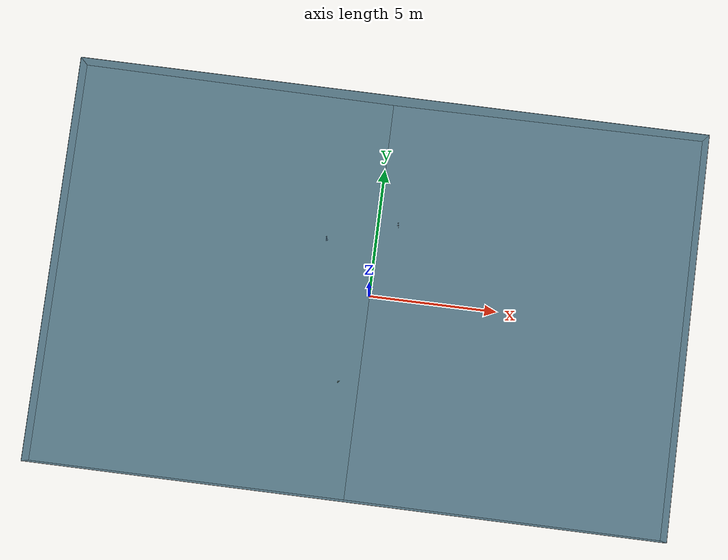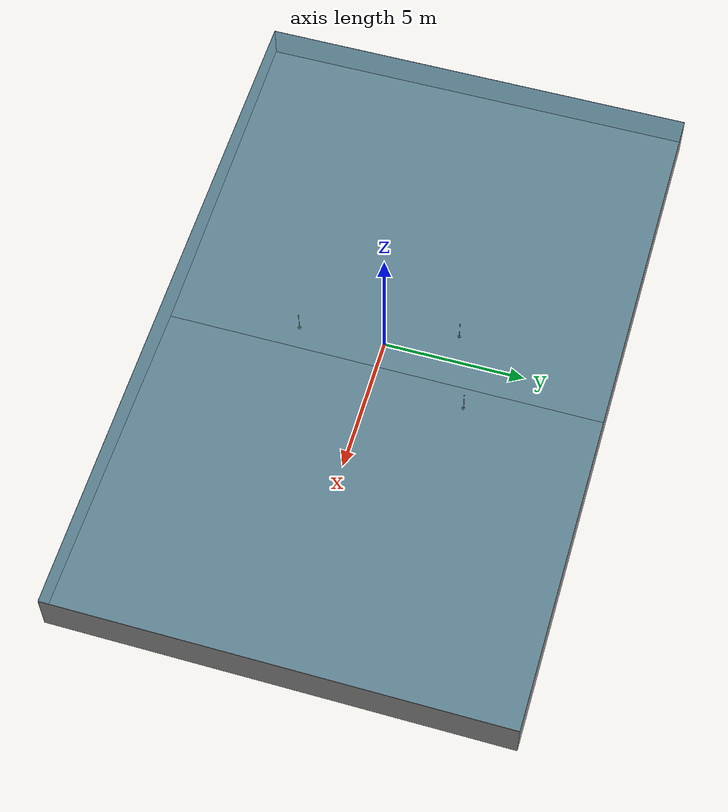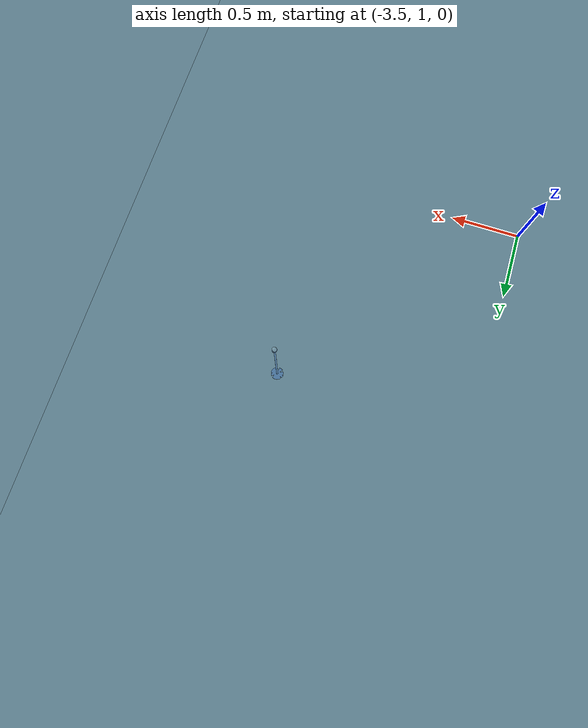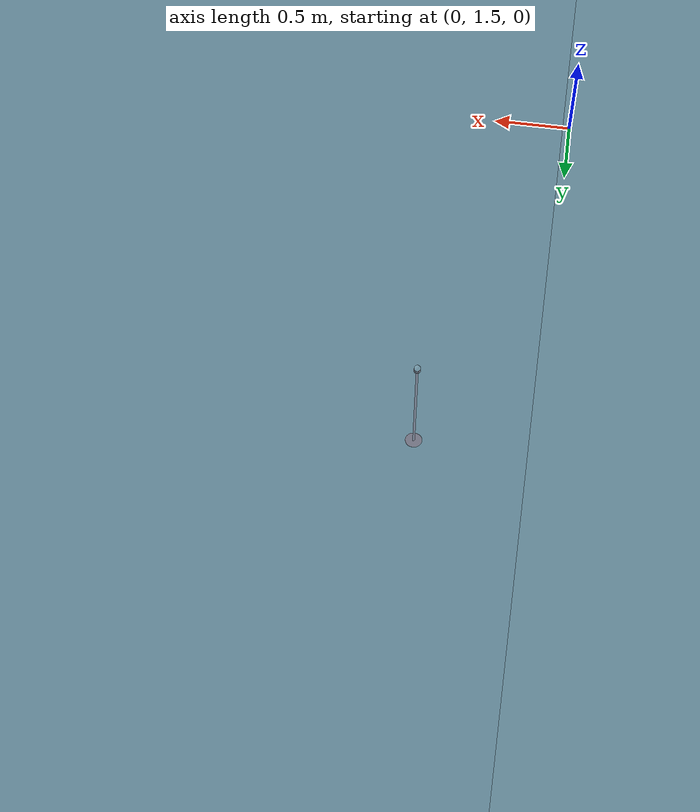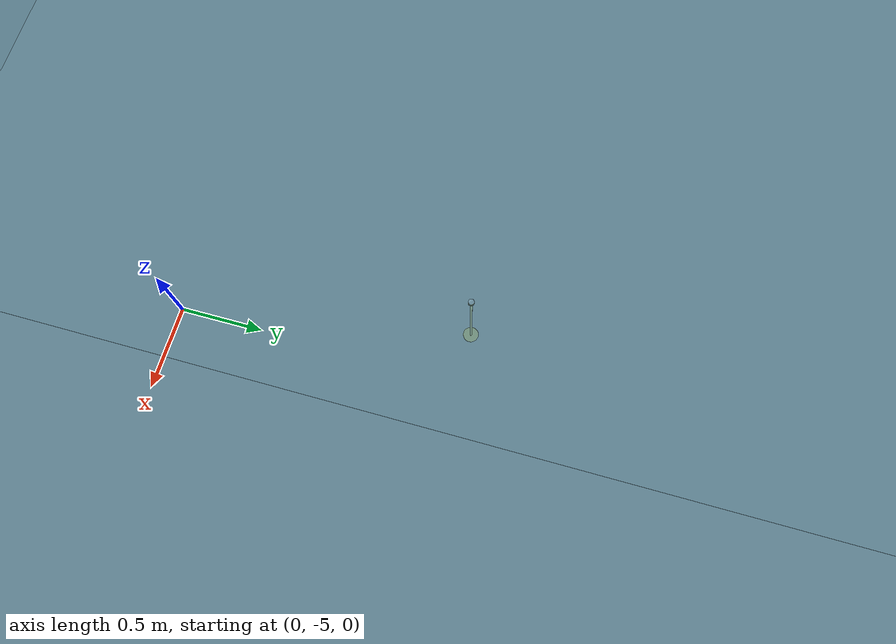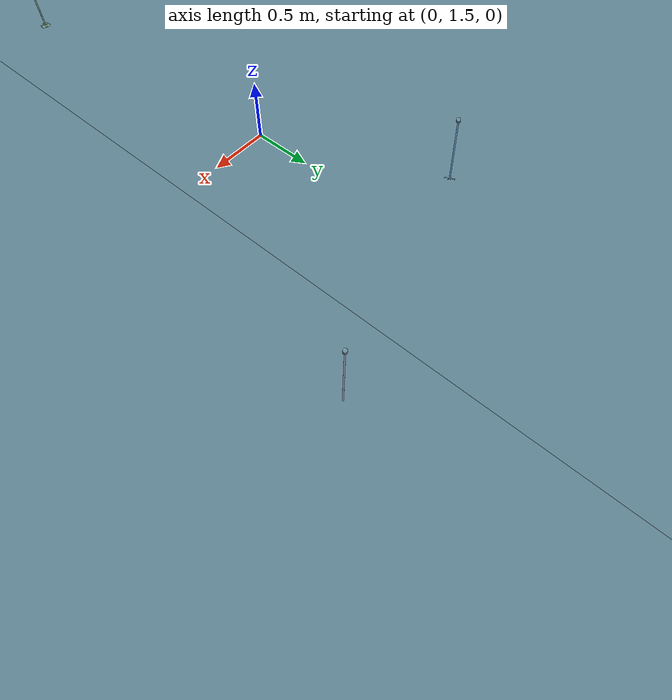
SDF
<sdf version="1.9">
 <world name="task_localization">
  <plugin filename="gz-sim-particle-emitter-system" name="gz::sim::systems::ParticleEmitter"/>
  <plugin filename="gz-sim-physics-system" name="gz::sim::systems::Physics"/>
  <plugin filename="gz-sim-user-commands-system" name="gz::sim::systems::UserCommands"/>
  <plugin filename="gz-sim-scene-broadcaster-system" name="gz::sim::systems::SceneBroadcaster"/>
  <plugin filename="gz-sim-apply-link-wrench-system" name="gz::sim::systems::ApplyLinkWrench"/>
  <plugin filename="gz-sim-imu-system" name="gz::sim::systems::Imu"/>
  <plugin filename="gz-sim-sensors-system" name="gz::sim::systems::Sensors">
   <render_engine>ogre2</render_engine>
  </plugin>
  <plugin filename="gz-sim-dvl-system" name="gz::sim::systems::DopplerVelocityLogSystem"/>
  <plugin filename="gz-sim-buoyancy-system" name="gz::sim::systems::Buoyancy">
   <graded_buoyancy>
    <default_density>1000</default_density>
    <density_change><above_depth>0</above_depth><density>1</density></density_change>
   </graded_buoyancy>
   <enable>mongla</enable>
   <enable>flare_red</enable>
   <enable>flare_red_ball</enable>
   <enable>flare_yellow</enable>
   <enable>flare_yellow_ball</enable>
   <enable>flare_blue</enable>
   <enable>flare_blue_ball</enable>
   <enable>payload_shot_0</enable>
   <enable>payload_shot_1</enable>
   <enable>payload_shot_2</enable>
   <enable>payload_shot_3</enable>
   <enable>payload_shot_4</enable>
   <enable>payload_shot_5</enable>
   <enable>payload_shot_6</enable>
   <enable>payload_shot_7</enable>
   <enable>payload_shot_8</enable>
   <enable>payload_shot_9</enable>
   <enable>payload_shot_10</enable>
   <enable>payload_shot_11</enable>
  </plugin>
  <physics name="default" type="dart">
   <max_step_size>0.001</max_step_size>
   <real_time_factor>1.0</real_time_factor>
   <real_time_update_rate>1000</real_time_update_rate>
   <dart>
    <collision_detector>bullet</collision_detector>
    <solver><solver_type>dantzig</solver_type></solver>
   </dart>
  </physics>
  <gravity>0 0 -9.81</gravity>
  <magnetic_field>3.9e-05 1.1e-06 2.6e-05</magnetic_field>
  <atmosphere type="adiabatic"/>
  <scene>
   <ambient>0.18 0.3 0.36 1</ambient>
   <background>0.08 0.26 0.4 1</background>
   <shadows>true</shadows>
   <fog>
    <color>0.1 0.26 0.3 1</color>
    <type>linear</type>
    <start>1.2</start>
    <end>16.0</end>
    <density>0.028</density>
   </fog>
  </scene>
  <light type="directional" name="sun">
   <pose>0 0 10 0 0 0</pose>
   <diffuse>0.48 0.52 0.56 1</diffuse>
   <specular>0.10 0.10 0.11 1</specular>
   <direction>-0.4 0.15 -0.9</direction>
  </light>
  <light type="directional" name="fill">
   <cast_shadows>false</cast_shadows>
   <pose>0 0 5 0 0 0</pose>
   <diffuse>0.22 0.28 0.34 1</diffuse>
   <specular>0.04 0.05 0.06 1</specular>
   <direction>0.3 -0.2 -1</direction>
  </light>
  <light type="directional" name="caustic_fill">
   <cast_shadows>false</cast_shadows>
   <pose>0 0 3 0 0 0</pose>
   <diffuse>0.12 0.22 0.26 1</diffuse>
   <specular>0.02 0.03 0.04 1</specular>
   <direction>0.1 0.35 -0.85</direction>
  </light>
  <model name="sauvc_pool">
   <static>true</static>
   <link name="floor_neg">
    <pose>-6.25 0 -1.4 0 0.0319891 0</pose>
    <inertial>
     <mass>1000</mass>
     <inertia><ixx>1000</ixx><ixy>0</ixy><ixz>0</ixz><iyy>1000</iyy><iyz>0</iyz><izz>1000</izz></inertia>
    </inertial>
    <visual name="floor_neg_visual">
     <pose>0 0 0.005 0 0 0</pose>
     <geometry><box><size>12.5064 16 0.01</size></box></geometry>
     <material>
      <ambient>0.55 0.55 0.55 1</ambient>
      <diffuse>0.55 0.55 0.55 1</diffuse>
      <specular>0.08 0.08 0.08 1</specular>
      <emissive>0 0 0 1</emissive>
      <pbr>
       <metal>
        <albedo_map>model://sauvc_textures/pool_floor_neg.png</albedo_map>
        <metalness>0.0</metalness>
        <roughness>0.85</roughness>
       </metal>
      </pbr>
     </material>
    </visual>
    <collision name="floor_neg_collision">
     <pose>0 0 -0.05 0 0 0</pose>
     <geometry><box><size>12.5064 16 0.1</size></box></geometry>
    </collision>
   </link>
   <link name="floor_pos">
    <pose>6.25 0 -1.4 0 -0.0319891 0</pose>
    <inertial>
     <mass>1000</mass>
     <inertia><ixx>1000</ixx><ixy>0</ixy><ixz>0</ixz><iyy>1000</iyy><iyz>0</iyz><izz>1000</izz></inertia>
    </inertial>
    <visual name="floor_pos_visual">
     <pose>0 0 0.005 0 0 0</pose>
     <geometry><box><size>12.5064 16 0.01</size></box></geometry>
     <material>
      <ambient>0.55 0.55 0.55 1</ambient>
      <diffuse>0.55 0.55 0.55 1</diffuse>
      <specular>0.08 0.08 0.08 1</specular>
      <emissive>0 0 0 1</emissive>
      <pbr>
       <metal>
        <albedo_map>model://sauvc_textures/pool_floor_pos.png</albedo_map>
        <metalness>0.0</metalness>
        <roughness>0.85</roughness>
       </metal>
      </pbr>
     </material>
    </visual>
    <collision name="floor_pos_collision">
     <pose>0 0 -0.05 0 0 0</pose>
     <geometry><box><size>12.5064 16 0.1</size></box></geometry>
    </collision>
   </link>
   <link name="wall_x_pos">
    <inertial>
     <mass>1000</mass>
     <inertia><ixx>1000</ixx><ixy>0</ixy><ixz>0</ixz><iyy>1000</iyy><iyz>0</iyz><izz>1000</izz></inertia>
    </inertial>
    <visual name="wall_x_pos_visual">
     <pose>12.5 0 -0.8 0 0 0</pose>
     <geometry><box><size>0.01 16 1.6</size></box></geometry>
     <material>
      <ambient>0.55 0.55 0.55 1</ambient>
      <diffuse>0.55 0.55 0.55 1</diffuse>
      <specular>0.08 0.08 0.08 1</specular>
      <emissive>0 0 0 1</emissive>
      <pbr>
       <metal>
        <albedo_map>model://sauvc_textures/pool_wall_long.png</albedo_map>
        <metalness>0.0</metalness>
        <roughness>0.85</roughness>
       </metal>
      </pbr>
     </material>
    </visual>
    <collision name="wall_x_pos_collision">
     <pose>12.605 0 -0.8 0 0 0</pose>
     <geometry><box><size>0.2 16.4 1.6</size></box></geometry>
    </collision>
   </link>
   <link name="wall_x_neg">
    <inertial>
     <mass>1000</mass>
     <inertia><ixx>1000</ixx><ixy>0</ixy><ixz>0</ixz><iyy>1000</iyy><iyz>0</iyz><izz>1000</izz></inertia>
    </inertial>
    <visual name="wall_x_neg_visual">
     <pose>-12.5 0 -0.8 0 0 0</pose>
     <geometry><box><size>0.01 16 1.6</size></box></geometry>
     <material>
      <ambient>0.55 0.55 0.55 1</ambient>
      <diffuse>0.55 0.55 0.55 1</diffuse>
      <specular>0.08 0.08 0.08 1</specular>
      <emissive>0 0 0 1</emissive>
      <pbr>
       <metal>
        <albedo_map>model://sauvc_textures/pool_wall_long.png</albedo_map>
        <metalness>0.0</metalness>
        <roughness>0.85</roughness>
       </metal>
      </pbr>
     </material>
    </visual>
    <collision name="wall_x_neg_collision">
     <pose>-12.605 0 -0.8 0 0 0</pose>
     <geometry><box><size>0.2 16.4 1.6</size></box></geometry>
    </collision>
   </link>
   <link name="wall_y_pos">
    <inertial>
     <mass>1000</mass>
     <inertia><ixx>1000</ixx><ixy>0</ixy><ixz>0</ixz><iyy>1000</iyy><iyz>0</iyz><izz>1000</izz></inertia>
    </inertial>
    <visual name="wall_y_pos_visual">
     <pose>0 8 -0.8 0 0 0</pose>
     <geometry><box><size>25 0.01 1.6</size></box></geometry>
     <material>
      <ambient>0.55 0.55 0.55 1</ambient>
      <diffuse>0.55 0.55 0.55 1</diffuse>
      <specular>0.08 0.08 0.08 1</specular>
      <emissive>0 0 0 1</emissive>
      <pbr>
       <metal>
        <albedo_map>model://sauvc_textures/pool_wall_short.png</albedo_map>
        <metalness>0.0</metalness>
        <roughness>0.85</roughness>
       </metal>
      </pbr>
     </material>
    </visual>
    <collision name="wall_y_pos_collision">
     <pose>0 8.105 -0.8 0 0 0</pose>
     <geometry><box><size>25 0.2 1.6</size></box></geometry>
    </collision>
   </link>
   <link name="wall_y_neg">
    <inertial>
     <mass>1000</mass>
     <inertia><ixx>1000</ixx><ixy>0</ixy><ixz>0</ixz><iyy>1000</iyy><iyz>0</iyz><izz>1000</izz></inertia>
    </inertial>
    <visual name="wall_y_neg_visual">
     <pose>0 -8 -0.8 0 0 0</pose>
     <geometry><box><size>25 0.01 1.6</size></box></geometry>
     <material>
      <ambient>0.55 0.55 0.55 1</ambient>
      <diffuse>0.55 0.55 0.55 1</diffuse>
      <specular>0.08 0.08 0.08 1</specular>
      <emissive>0 0 0 1</emissive>
      <pbr>
       <metal>
        <albedo_map>model://sauvc_textures/pool_wall_short.png</albedo_map>
        <metalness>0.0</metalness>
        <roughness>0.85</roughness>
       </metal>
      </pbr>
     </material>
    </visual>
    <collision name="wall_y_neg_collision">
     <pose>0 -8.105 -0.8 0 0 0</pose>
     <geometry><box><size>25 0.2 1.6</size></box></geometry>
    </collision>
   </link>
   <link name="water_surface">
    <inertial>
     <mass>1</mass>
     <inertia><ixx>1</ixx><ixy>0</ixy><ixz>0</ixz><iyy>1</iyy><iyz>0</iyz><izz>1</izz></inertia>
    </inertial>
    <visual name="water_surface_visual">
     <cast_shadows>false</cast_shadows>
     <transparency>0.18</transparency>
     <geometry><mesh><uri>model://robosub_meshes/meshes/water_sauvc.obj</uri></mesh></geometry>
     <material>
      <ambient>0.42 0.6 0.68 1</ambient>
      <diffuse>0.42 0.6 0.68 1</diffuse>
      <specular>0.35 0.35 0.35 1</specular>
      <emissive>0.1 0.1 0.1 1</emissive>
      <pbr>
       <metal>
        <albedo_map>model://sauvc_textures/water_surface.png</albedo_map>
        <metalness>0.0</metalness>
        <roughness>0.15</roughness>
       </metal>
      </pbr>
     </material>
    </visual>
   </link>
  </model>
  <model name="marine_snow">
   <static>true</static>
   <pose>0 0 -0.8 0 0 0</pose>
   <link name="link">
    <particle_emitter name="snow" type="box">
     <emitting>true</emitting>
     <size>12 12 1.6</size>
     <particle_size>0.006 0.006 0.006</particle_size>
     <lifetime>30</lifetime>
     <min_velocity>0.004</min_velocity>
     <max_velocity>0.025</max_velocity>
     <scale_rate>0</scale_rate>
     <rate>900</rate>
     <topic>marine_snow</topic>
     <material>
      <diffuse>0.80 0.84 0.80</diffuse>
      <specular>0.05 0.05 0.05</specular>
      <pbr><metal><albedo_map>model://sauvc_textures/marine_snow.png</albedo_map></metal></pbr>
     </material>
    </particle_emitter>
   </link>
  </model>
  <include>
   <uri>model://sauvc_flare_red</uri>
   <name>flare_red</name>
   <pose>0.8 3.1 -1.5744 -0 -0.0319891 0</pose>
  </include>
  <include>
   <uri>model://sauvc_golf_ball</uri>
   <name>flare_red_ball</name>
   <pose>0.773538 3.1 -0.747473 0 0 0</pose>
  </include>
  <include>
   <uri>model://sauvc_flare_yellow</uri>
   <name>flare_yellow</name>
   <pose>-0.8 -3.4 -1.5744 0 0.0319891 0</pose>
  </include>
  <include>
   <uri>model://sauvc_golf_ball</uri>
   <name>flare_yellow_ball</name>
   <pose>-0.773538 -3.4 -0.747473 0 0 0</pose>
  </include>
  <include>
   <uri>model://sauvc_flare_blue</uri>
   <name>flare_blue</name>
   <pose>-2 2.2 -1.536 0 0.0319891 0</pose>
  </include>
  <include>
   <uri>model://sauvc_golf_ball</uri>
   <name>flare_blue_ball</name>
   <pose>-1.97354 2.2 -0.709073 0 0 0</pose>
  </include>
 </world>
</sdf>

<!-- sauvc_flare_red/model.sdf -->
<sdf version="1.9">
  <model name="sauvc_flare_red">
    <static>false</static>
    <plugin filename="gz-sim-label-system" name="gz::sim::systems::Label">
      <label>4</label>
    </plugin>
    <link name="pole">
      <pose>0 0 0.4 0 0 0</pose>
      <inertial>
        <pose>0 0 0 0 0 0</pose>
        <mass>0.02</mass>
        <inertia>
          <ixx>0.00106699</ixx><ixy>0</ixy><ixz>0</ixz>
          <iyy>0.00106699</iyy><iyz>0</iyz>
          <izz>6.4e-07</izz>
        </inertia>
      </inertial>
      <visual name="pole_visual">
        <pose>0 0 0 0 0 0</pose>
        <geometry><cylinder><radius>0.008</radius><length>0.8</length></cylinder></geometry>
        <material>
          <ambient>0.88 0.08 0.08 1</ambient>
          <diffuse>0.88 0.08 0.08 1</diffuse>
          <specular>0.55 0.55 0.55 1</specular>
          <emissive>0.246 0.0224 0.0224 1</emissive>
          <pbr>
            <metal>
              <albedo_map>model://sauvc_textures/albedo_pvc.png</albedo_map>
              <metalness>0.0</metalness>
              <roughness_map>model://sauvc_textures/rough_pvc.png</roughness_map>
              <normal_map>model://sauvc_textures/norm_pvc.png</normal_map>
            </metal>
          </pbr>
        </material>
      </visual>
      <collision name="pole_collision">
        <pose>0 0 0 0 0 0</pose>
        <geometry><cylinder><radius>0.008</radius><length>0.8</length></cylinder></geometry>
      </collision>
    </link>
    <link name="cup_floor">
      <pose>0 0 0.803 0 0 0</pose>
      <inertial>
        <pose>0 0 0 0 0 0</pose>
        <mass>0.008</mass>
        <inertia>
          <ixx>1.02909e-06</ixx><ixy>0</ixy><ixz>0</ixz>
          <iyy>1.02909e-06</iyy><iyz>0</iyz>
          <izz>2.01018e-06</izz>
        </inertia>
      </inertial>
      <visual name="cup_floor_visual">
        <pose>0 0 0 0 0 0</pose>
        <geometry><cylinder><radius>0.0224175</radius><length>0.006</length></cylinder></geometry>
        <material>
          <ambient>0.88 0.08 0.08 1</ambient>
          <diffuse>0.88 0.08 0.08 1</diffuse>
          <specular>0.55 0.55 0.55 1</specular>
          <emissive>0.246 0.0224 0.0224 1</emissive>
          <pbr>
            <metal>
              <albedo_map>model://sauvc_textures/albedo_pvc.png</albedo_map>
              <metalness>0.0</metalness>
              <roughness_map>model://sauvc_textures/rough_pvc.png</roughness_map>
              <normal_map>model://sauvc_textures/norm_pvc.png</normal_map>
            </metal>
          </pbr>
        </material>
      </visual>
      <collision name="cup_floor_collision">
        <pose>0 0 0 0 0 0</pose>
        <geometry><cylinder><radius>0.0224175</radius><length>0.006</length></cylinder></geometry>
      </collision>
    </link>
    <link name="base">
      <pose>0 0 0.005 0 0 0</pose>
      <inertial>
        <pose>0 0 0 0 0 0</pose>
        <mass>0.6</mass>
        <inertia>
          <ixx>0.000545</ixx><ixy>0</ixy><ixz>0</ixz>
          <iyy>0.000545</iyy><iyz>0</iyz>
          <izz>0.00108</izz>
        </inertia>
      </inertial>
      <visual name="base_visual">
        <pose>0 0 0 0 0 0</pose>
        <geometry><cylinder><radius>0.06</radius><length>0.01</length></cylinder></geometry>
        <material>
          <ambient>0.88 0.08 0.08 1</ambient>
          <diffuse>0.88 0.08 0.08 1</diffuse>
          <specular>0.55 0.55 0.55 1</specular>
          <emissive>0.246 0.0224 0.0224 1</emissive>
          <pbr>
            <metal>
              <albedo_map>model://sauvc_textures/albedo_pvc.png</albedo_map>
              <metalness>0.0</metalness>
              <roughness_map>model://sauvc_textures/rough_pvc.png</roughness_map>
              <normal_map>model://sauvc_textures/norm_pvc.png</normal_map>
            </metal>
          </pbr>
        </material>
      </visual>
      <collision name="base_collision">
        <pose>0 0 0 0 0 0</pose>
        <geometry><cylinder><radius>0.06</radius><length>0.01</length></cylinder></geometry>
        <surface>
          <friction>
            <ode><mu>0.8</mu><mu2>0.8</mu2></ode>
            <bullet><friction>0.8</friction><friction2>0.8</friction2></bullet>
          </friction>
        </surface>
      </collision>
    </link>
    <link name="cup_rim_0">
      <pose>0.019642 0 0.812 0 0 0</pose>
      <inertial>
        <pose>0 0 0 0 0 0</pose>
        <mass>0.0015</mass>
        <inertia>
          <ixx>6.68433e-08</ixx><ixy>0</ixy><ixz>0</ixz>
          <iyy>3.4e-08</iyy><iyz>0</iyz>
          <izz>3.68433e-08</izz>
        </inertia>
      </inertial>
      <visual name="cup_rim_0_visual">
        <pose>0 0 0 0 0 0</pose>
        <geometry><box><size>0.004 0.0166957 0.016</size></box></geometry>
        <material>
          <ambient>0.88 0.08 0.08 1</ambient>
          <diffuse>0.88 0.08 0.08 1</diffuse>
          <specular>0.55 0.55 0.55 1</specular>
          <emissive>0.246 0.0224 0.0224 1</emissive>
          <pbr>
            <metal>
              <albedo_map>model://sauvc_textures/albedo_pvc.png</albedo_map>
              <metalness>0.0</metalness>
              <roughness_map>model://sauvc_textures/rough_pvc.png</roughness_map>
              <normal_map>model://sauvc_textures/norm_pvc.png</normal_map>
            </metal>
          </pbr>
        </material>
      </visual>
      <collision name="cup_rim_0_collision">
        <pose>0 0 0 0 0 0</pose>
        <geometry><box><size>0.004 0.0166957 0.016</size></box></geometry>
      </collision>
    </link>
    <link name="cup_rim_1">
      <pose>0.013889 0.013889 0.812 0 0 0.785398</pose>
      <inertial>
        <pose>0 0 0 0 0 0</pose>
        <mass>0.0015</mass>
        <inertia>
          <ixx>6.68433e-08</ixx><ixy>0</ixy><ixz>0</ixz>
          <iyy>3.4e-08</iyy><iyz>0</iyz>
          <izz>3.68433e-08</izz>
        </inertia>
      </inertial>
      <visual name="cup_rim_1_visual">
        <pose>0 0 0 0 0 0</pose>
        <geometry><box><size>0.004 0.0166957 0.016</size></box></geometry>
        <material>
          <ambient>0.88 0.08 0.08 1</ambient>
          <diffuse>0.88 0.08 0.08 1</diffuse>
          <specular>0.55 0.55 0.55 1</specular>
          <emissive>0.246 0.0224 0.0224 1</emissive>
          <pbr>
            <metal>
              <albedo_map>model://sauvc_textures/albedo_pvc.png</albedo_map>
              <metalness>0.0</metalness>
              <roughness_map>model://sauvc_textures/rough_pvc.png</roughness_map>
              <normal_map>model://sauvc_textures/norm_pvc.png</normal_map>
            </metal>
          </pbr>
        </material>
      </visual>
      <collision name="cup_rim_1_collision">
        <pose>0 0 0 0 0 0</pose>
        <geometry><box><size>0.004 0.0166957 0.016</size></box></geometry>
      </collision>
    </link>
    <link name="cup_rim_2">
      <pose>1.20273e-18 0.019642 0.812 0 0 1.5708</pose>
      <inertial>
        <pose>0 0 0 0 0 0</pose>
        <mass>0.0015</mass>
        <inertia>
          <ixx>6.68433e-08</ixx><ixy>0</ixy><ixz>0</ixz>
          <iyy>3.4e-08</iyy><iyz>0</iyz>
          <izz>3.68433e-08</izz>
        </inertia>
      </inertial>
      <visual name="cup_rim_2_visual">
        <pose>0 0 0 0 0 0</pose>
        <geometry><box><size>0.004 0.0166957 0.016</size></box></geometry>
        <material>
          <ambient>0.88 0.08 0.08 1</ambient>
          <diffuse>0.88 0.08 0.08 1</diffuse>
          <specular>0.55 0.55 0.55 1</specular>
          <emissive>0.246 0.0224 0.0224 1</emissive>
          <pbr>
            <metal>
              <albedo_map>model://sauvc_textures/albedo_pvc.png</albedo_map>
              <metalness>0.0</metalness>
              <roughness_map>model://sauvc_textures/rough_pvc.png</roughness_map>
              <normal_map>model://sauvc_textures/norm_pvc.png</normal_map>
            </metal>
          </pbr>
        </material>
      </visual>
      <collision name="cup_rim_2_collision">
        <pose>0 0 0 0 0 0</pose>
        <geometry><box><size>0.004 0.0166957 0.016</size></box></geometry>
      </collision>
    </link>
    <link name="cup_rim_3">
      <pose>-0.013889 0.013889 0.812 0 0 2.35619</pose>
      <inertial>
        <pose>0 0 0 0 0 0</pose>
        <mass>0.0015</mass>
        <inertia>
          <ixx>6.68433e-08</ixx><ixy>0</ixy><ixz>0</ixz>
          <iyy>3.4e-08</iyy><iyz>0</iyz>
          <izz>3.68433e-08</izz>
        </inertia>
      </inertial>
      <visual name="cup_rim_3_visual">
        <pose>0 0 0 0 0 0</pose>
        <geometry><box><size>0.004 0.0166957 0.016</size></box></geometry>
        <material>
          <ambient>0.88 0.08 0.08 1</ambient>
          <diffuse>0.88 0.08 0.08 1</diffuse>
          <specular>0.55 0.55 0.55 1</specular>
          <emissive>0.246 0.0224 0.0224 1</emissive>
          <pbr>
            <metal>
              <albedo_map>model://sauvc_textures/albedo_pvc.png</albedo_map>
              <metalness>0.0</metalness>
              <roughness_map>model://sauvc_textures/rough_pvc.png</roughness_map>
              <normal_map>model://sauvc_textures/norm_pvc.png</normal_map>
            </metal>
          </pbr>
        </material>
      </visual>
      <collision name="cup_rim_3_collision">
        <pose>0 0 0 0 0 0</pose>
        <geometry><box><size>0.004 0.0166957 0.016</size></box></geometry>
      </collision>
    </link>
    <link name="cup_rim_4">
      <pose>-0.019642 2.40545e-18 0.812 0 0 3.14159</pose>
      <inertial>
        <pose>0 0 0 0 0 0</pose>
        <mass>0.0015</mass>
        <inertia>
          <ixx>6.68433e-08</ixx><ixy>0</ixy><ixz>0</ixz>
          <iyy>3.4e-08</iyy><iyz>0</iyz>
          <izz>3.68433e-08</izz>
        </inertia>
      </inertial>
      <visual name="cup_rim_4_visual">
        <pose>0 0 0 0 0 0</pose>
        <geometry><box><size>0.004 0.0166957 0.016</size></box></geometry>
        <material>
          <ambient>0.88 0.08 0.08 1</ambient>
          <diffuse>0.88 0.08 0.08 1</diffuse>
          <specular>0.55 0.55 0.55 1</specular>
          <emissive>0.246 0.0224 0.0224 1</emissive>
          <pbr>
            <metal>
              <albedo_map>model://sauvc_textures/albedo_pvc.png</albedo_map>
              <metalness>0.0</metalness>
              <roughness_map>model://sauvc_textures/rough_pvc.png</roughness_map>
              <normal_map>model://sauvc_textures/norm_pvc.png</normal_map>
            </metal>
          </pbr>
        </material>
      </visual>
      <collision name="cup_rim_4_collision">
        <pose>0 0 0 0 0 0</pose>
        <geometry><box><size>0.004 0.0166957 0.016</size></box></geometry>
      </collision>
    </link>
    <link name="cup_rim_5">
      <pose>-0.013889 -0.013889 0.812 0 0 3.92699</pose>
      <inertial>
        <pose>0 0 0 0 0 0</pose>
        <mass>0.0015</mass>
        <inertia>
          <ixx>6.68433e-08</ixx><ixy>0</ixy><ixz>0</ixz>
          <iyy>3.4e-08</iyy><iyz>0</iyz>
          <izz>3.68433e-08</izz>
        </inertia>
      </inertial>
      <visual name="cup_rim_5_visual">
        <pose>0 0 0 0 0 0</pose>
        <geometry><box><size>0.004 0.0166957 0.016</size></box></geometry>
        <material>
          <ambient>0.88 0.08 0.08 1</ambient>
          <diffuse>0.88 0.08 0.08 1</diffuse>
          <specular>0.55 0.55 0.55 1</specular>
          <emissive>0.246 0.0224 0.0224 1</emissive>
          <pbr>
            <metal>
              <albedo_map>model://sauvc_textures/albedo_pvc.png</albedo_map>
              <metalness>0.0</metalness>
              <roughness_map>model://sauvc_textures/rough_pvc.png</roughness_map>
              <normal_map>model://sauvc_textures/norm_pvc.png</normal_map>
            </metal>
          </pbr>
        </material>
      </visual>
      <collision name="cup_rim_5_collision">
        <pose>0 0 0 0 0 0</pose>
        <geometry><box><size>0.004 0.0166957 0.016</size></box></geometry>
      </collision>
    </link>
    <link name="cup_rim_6">
      <pose>-3.60818e-18 -0.019642 0.812 0 0 4.71239</pose>
      <inertial>
        <pose>0 0 0 0 0 0</pose>
        <mass>0.0015</mass>
        <inertia>
          <ixx>6.68433e-08</ixx><ixy>0</ixy><ixz>0</ixz>
          <iyy>3.4e-08</iyy><iyz>0</iyz>
          <izz>3.68433e-08</izz>
        </inertia>
      </inertial>
      <visual name="cup_rim_6_visual">
        <pose>0 0 0 0 0 0</pose>
        <geometry><box><size>0.004 0.0166957 0.016</size></box></geometry>
        <material>
          <ambient>0.88 0.08 0.08 1</ambient>
          <diffuse>0.88 0.08 0.08 1</diffuse>
          <specular>0.55 0.55 0.55 1</specular>
          <emissive>0.246 0.0224 0.0224 1</emissive>
          <pbr>
            <metal>
              <albedo_map>model://sauvc_textures/albedo_pvc.png</albedo_map>
              <metalness>0.0</metalness>
              <roughness_map>model://sauvc_textures/rough_pvc.png</roughness_map>
              <normal_map>model://sauvc_textures/norm_pvc.png</normal_map>
            </metal>
          </pbr>
        </material>
      </visual>
      <collision name="cup_rim_6_collision">
        <pose>0 0 0 0 0 0</pose>
        <geometry><box><size>0.004 0.0166957 0.016</size></box></geometry>
      </collision>
    </link>
    <link name="cup_rim_7">
      <pose>0.013889 -0.013889 0.812 0 0 5.49779</pose>
      <inertial>
        <pose>0 0 0 0 0 0</pose>
        <mass>0.0015</mass>
        <inertia>
          <ixx>6.68433e-08</ixx><ixy>0</ixy><ixz>0</ixz>
          <iyy>3.4e-08</iyy><iyz>0</iyz>
          <izz>3.68433e-08</izz>
        </inertia>
      </inertial>
      <visual name="cup_rim_7_visual">
        <pose>0 0 0 0 0 0</pose>
        <geometry><box><size>0.004 0.0166957 0.016</size></box></geometry>
        <material>
          <ambient>0.88 0.08 0.08 1</ambient>
          <diffuse>0.88 0.08 0.08 1</diffuse>
          <specular>0.55 0.55 0.55 1</specular>
          <emissive>0.246 0.0224 0.0224 1</emissive>
          <pbr>
            <metal>
              <albedo_map>model://sauvc_textures/albedo_pvc.png</albedo_map>
              <metalness>0.0</metalness>
              <roughness_map>model://sauvc_textures/rough_pvc.png</roughness_map>
              <normal_map>model://sauvc_textures/norm_pvc.png</normal_map>
            </metal>
          </pbr>
        </material>
      </visual>
      <collision name="cup_rim_7_collision">
        <pose>0 0 0 0 0 0</pose>
        <geometry><box><size>0.004 0.0166957 0.016</size></box></geometry>
      </collision>
    </link>
    <joint name="base_pole_fix" type="fixed">
      <parent>base</parent>
      <child>pole</child>
    </joint>
    <joint name="base_cup_floor_fix" type="fixed">
      <parent>base</parent>
      <child>cup_floor</child>
    </joint>
    <joint name="base_cup_rim_0_fix" type="fixed">
      <parent>base</parent>
      <child>cup_rim_0</child>
    </joint>
    <joint name="base_cup_rim_1_fix" type="fixed">
      <parent>base</parent>
      <child>cup_rim_1</child>
    </joint>
    <joint name="base_cup_rim_2_fix" type="fixed">
      <parent>base</parent>
      <child>cup_rim_2</child>
    </joint>
    <joint name="base_cup_rim_3_fix" type="fixed">
      <parent>base</parent>
      <child>cup_rim_3</child>
    </joint>
    <joint name="base_cup_rim_4_fix" type="fixed">
      <parent>base</parent>
      <child>cup_rim_4</child>
    </joint>
    <joint name="base_cup_rim_5_fix" type="fixed">
      <parent>base</parent>
      <child>cup_rim_5</child>
    </joint>
    <joint name="base_cup_rim_6_fix" type="fixed">
      <parent>base</parent>
      <child>cup_rim_6</child>
    </joint>
    <joint name="base_cup_rim_7_fix" type="fixed">
      <parent>base</parent>
      <child>cup_rim_7</child>
    </joint>
    <plugin filename="gz-sim-hydrodynamics-system" name="gz::sim::systems::Hydrodynamics">
      <link_name>pole</link_name>
      <water_density>1000.0</water_density>
      <xUabsU>-6.4</xUabsU>
      <yVabsV>-6.4</yVabsV>
      <zWabsW>-0.100531</zWabsW>
      <kPabsP>-0.8192</kPabsP>
      <mQabsQ>-0.8192</mQabsQ>
      <nRabsR>-0.8192</nRabsR>
    </plugin>
  </model>
</sdf>

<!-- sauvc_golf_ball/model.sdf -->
<sdf version="1.9">
  <model name="sauvc_golf_ball">
    <static>false</static>
    <plugin filename="gz-sim-label-system" name="gz::sim::systems::Label">
      <label>26</label>
    </plugin>
    <link name="ball">
      <pose>0 0 0 0 0 0</pose>
      <inertial>
        <pose>0 0 0 0 0 0</pose>
        <mass>0.0459</mass>
        <inertia>
          <ixx>8.3689e-06</ixx><ixy>0</ixy><ixz>0</ixz>
          <iyy>8.3689e-06</iyy><iyz>0</iyz>
          <izz>8.3689e-06</izz>
        </inertia>
      </inertial>
      <visual name="ball_visual">
        <pose>0 0 0 0 0 0</pose>
        <geometry><sphere><radius>0.02135</radius></sphere></geometry>
        <material>
          <ambient>0.95 0.95 0.95 1</ambient>
          <diffuse>0.95 0.95 0.95 1</diffuse>
          <specular>0.2 0.2 0.2 1</specular>
          <emissive>0.2375 0.2375 0.2375 1</emissive>
        </material>
      </visual>
      <collision name="ball_collision">
        <pose>0 0 0 0 0 0</pose>
        <geometry><sphere><radius>0.02135</radius></sphere></geometry>
      </collision>
    </link>
  </model>
</sdf>

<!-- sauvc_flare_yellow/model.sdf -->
<sdf version="1.9">
  <model name="sauvc_flare_yellow">
    <static>false</static>
    <plugin filename="gz-sim-label-system" name="gz::sim::systems::Label">
      <label>5</label>
    </plugin>
    <link name="pole">
      <pose>0 0 0.4 0 0 0</pose>
      <inertial>
        <pose>0 0 0 0 0 0</pose>
        <mass>0.02</mass>
        <inertia>
          <ixx>0.00106699</ixx><ixy>0</ixy><ixz>0</ixz>
          <iyy>0.00106699</iyy><iyz>0</iyz>
          <izz>6.4e-07</izz>
        </inertia>
      </inertial>
      <visual name="pole_visual">
        <pose>0 0 0 0 0 0</pose>
        <geometry><cylinder><radius>0.008</radius><length>0.8</length></cylinder></geometry>
        <material>
          <ambient>0.95 0.85 0.05 1</ambient>
          <diffuse>0.95 0.85 0.05 1</diffuse>
          <specular>0.55 0.55 0.55 1</specular>
          <emissive>0.266 0.238 0.014 1</emissive>
          <pbr>
            <metal>
              <albedo_map>model://sauvc_textures/albedo_pvc.png</albedo_map>
              <metalness>0.0</metalness>
              <roughness_map>model://sauvc_textures/rough_pvc.png</roughness_map>
              <normal_map>model://sauvc_textures/norm_pvc.png</normal_map>
            </metal>
          </pbr>
        </material>
      </visual>
      <collision name="pole_collision">
        <pose>0 0 0 0 0 0</pose>
        <geometry><cylinder><radius>0.008</radius><length>0.8</length></cylinder></geometry>
      </collision>
    </link>
    <link name="cup_floor">
      <pose>0 0 0.803 0 0 0</pose>
      <inertial>
        <pose>0 0 0 0 0 0</pose>
        <mass>0.008</mass>
        <inertia>
          <ixx>1.02909e-06</ixx><ixy>0</ixy><ixz>0</ixz>
          <iyy>1.02909e-06</iyy><iyz>0</iyz>
          <izz>2.01018e-06</izz>
        </inertia>
      </inertial>
      <visual name="cup_floor_visual">
        <pose>0 0 0 0 0 0</pose>
        <geometry><cylinder><radius>0.0224175</radius><length>0.006</length></cylinder></geometry>
        <material>
          <ambient>0.95 0.85 0.05 1</ambient>
          <diffuse>0.95 0.85 0.05 1</diffuse>
          <specular>0.55 0.55 0.55 1</specular>
          <emissive>0.266 0.238 0.014 1</emissive>
          <pbr>
            <metal>
              <albedo_map>model://sauvc_textures/albedo_pvc.png</albedo_map>
              <metalness>0.0</metalness>
              <roughness_map>model://sauvc_textures/rough_pvc.png</roughness_map>
              <normal_map>model://sauvc_textures/norm_pvc.png</normal_map>
            </metal>
          </pbr>
        </material>
      </visual>
      <collision name="cup_floor_collision">
        <pose>0 0 0 0 0 0</pose>
        <geometry><cylinder><radius>0.0224175</radius><length>0.006</length></cylinder></geometry>
      </collision>
    </link>
    <link name="base">
      <pose>0 0 0.005 0 0 0</pose>
      <inertial>
        <pose>0 0 0 0 0 0</pose>
        <mass>0.6</mass>
        <inertia>
          <ixx>0.000545</ixx><ixy>0</ixy><ixz>0</ixz>
          <iyy>0.000545</iyy><iyz>0</iyz>
          <izz>0.00108</izz>
        </inertia>
      </inertial>
      <visual name="base_visual">
        <pose>0 0 0 0 0 0</pose>
        <geometry><cylinder><radius>0.06</radius><length>0.01</length></cylinder></geometry>
        <material>
          <ambient>0.95 0.85 0.05 1</ambient>
          <diffuse>0.95 0.85 0.05 1</diffuse>
          <specular>0.55 0.55 0.55 1</specular>
          <emissive>0.266 0.238 0.014 1</emissive>
          <pbr>
            <metal>
              <albedo_map>model://sauvc_textures/albedo_pvc.png</albedo_map>
              <metalness>0.0</metalness>
              <roughness_map>model://sauvc_textures/rough_pvc.png</roughness_map>
              <normal_map>model://sauvc_textures/norm_pvc.png</normal_map>
            </metal>
          </pbr>
        </material>
      </visual>
      <collision name="base_collision">
        <pose>0 0 0 0 0 0</pose>
        <geometry><cylinder><radius>0.06</radius><length>0.01</length></cylinder></geometry>
        <surface>
          <friction>
            <ode><mu>0.8</mu><mu2>0.8</mu2></ode>
            <bullet><friction>0.8</friction><friction2>0.8</friction2></bullet>
          </friction>
        </surface>
      </collision>
    </link>
    <link name="cup_rim_0">
      <pose>0.019642 0 0.812 0 0 0</pose>
      <inertial>
        <pose>0 0 0 0 0 0</pose>
        <mass>0.0015</mass>
        <inertia>
          <ixx>6.68433e-08</ixx><ixy>0</ixy><ixz>0</ixz>
          <iyy>3.4e-08</iyy><iyz>0</iyz>
          <izz>3.68433e-08</izz>
        </inertia>
      </inertial>
      <visual name="cup_rim_0_visual">
        <pose>0 0 0 0 0 0</pose>
        <geometry><box><size>0.004 0.0166957 0.016</size></box></geometry>
        <material>
          <ambient>0.95 0.85 0.05 1</ambient>
          <diffuse>0.95 0.85 0.05 1</diffuse>
          <specular>0.55 0.55 0.55 1</specular>
          <emissive>0.266 0.238 0.014 1</emissive>
          <pbr>
            <metal>
              <albedo_map>model://sauvc_textures/albedo_pvc.png</albedo_map>
              <metalness>0.0</metalness>
              <roughness_map>model://sauvc_textures/rough_pvc.png</roughness_map>
              <normal_map>model://sauvc_textures/norm_pvc.png</normal_map>
            </metal>
          </pbr>
        </material>
      </visual>
      <collision name="cup_rim_0_collision">
        <pose>0 0 0 0 0 0</pose>
        <geometry><box><size>0.004 0.0166957 0.016</size></box></geometry>
      </collision>
    </link>
    <link name="cup_rim_1">
      <pose>0.013889 0.013889 0.812 0 0 0.785398</pose>
      <inertial>
        <pose>0 0 0 0 0 0</pose>
        <mass>0.0015</mass>
        <inertia>
          <ixx>6.68433e-08</ixx><ixy>0</ixy><ixz>0</ixz>
          <iyy>3.4e-08</iyy><iyz>0</iyz>
          <izz>3.68433e-08</izz>
        </inertia>
      </inertial>
      <visual name="cup_rim_1_visual">
        <pose>0 0 0 0 0 0</pose>
        <geometry><box><size>0.004 0.0166957 0.016</size></box></geometry>
        <material>
          <ambient>0.95 0.85 0.05 1</ambient>
          <diffuse>0.95 0.85 0.05 1</diffuse>
          <specular>0.55 0.55 0.55 1</specular>
          <emissive>0.266 0.238 0.014 1</emissive>
          <pbr>
            <metal>
              <albedo_map>model://sauvc_textures/albedo_pvc.png</albedo_map>
              <metalness>0.0</metalness>
              <roughness_map>model://sauvc_textures/rough_pvc.png</roughness_map>
              <normal_map>model://sauvc_textures/norm_pvc.png</normal_map>
            </metal>
          </pbr>
        </material>
      </visual>
      <collision name="cup_rim_1_collision">
        <pose>0 0 0 0 0 0</pose>
        <geometry><box><size>0.004 0.0166957 0.016</size></box></geometry>
      </collision>
    </link>
    <link name="cup_rim_2">
      <pose>1.20273e-18 0.019642 0.812 0 0 1.5708</pose>
      <inertial>
        <pose>0 0 0 0 0 0</pose>
        <mass>0.0015</mass>
        <inertia>
          <ixx>6.68433e-08</ixx><ixy>0</ixy><ixz>0</ixz>
          <iyy>3.4e-08</iyy><iyz>0</iyz>
          <izz>3.68433e-08</izz>
        </inertia>
      </inertial>
      <visual name="cup_rim_2_visual">
        <pose>0 0 0 0 0 0</pose>
        <geometry><box><size>0.004 0.0166957 0.016</size></box></geometry>
        <material>
          <ambient>0.95 0.85 0.05 1</ambient>
          <diffuse>0.95 0.85 0.05 1</diffuse>
          <specular>0.55 0.55 0.55 1</specular>
          <emissive>0.266 0.238 0.014 1</emissive>
          <pbr>
            <metal>
              <albedo_map>model://sauvc_textures/albedo_pvc.png</albedo_map>
              <metalness>0.0</metalness>
              <roughness_map>model://sauvc_textures/rough_pvc.png</roughness_map>
              <normal_map>model://sauvc_textures/norm_pvc.png</normal_map>
            </metal>
          </pbr>
        </material>
      </visual>
      <collision name="cup_rim_2_collision">
        <pose>0 0 0 0 0 0</pose>
        <geometry><box><size>0.004 0.0166957 0.016</size></box></geometry>
      </collision>
    </link>
    <link name="cup_rim_3">
      <pose>-0.013889 0.013889 0.812 0 0 2.35619</pose>
      <inertial>
        <pose>0 0 0 0 0 0</pose>
        <mass>0.0015</mass>
        <inertia>
          <ixx>6.68433e-08</ixx><ixy>0</ixy><ixz>0</ixz>
          <iyy>3.4e-08</iyy><iyz>0</iyz>
          <izz>3.68433e-08</izz>
        </inertia>
      </inertial>
      <visual name="cup_rim_3_visual">
        <pose>0 0 0 0 0 0</pose>
        <geometry><box><size>0.004 0.0166957 0.016</size></box></geometry>
        <material>
          <ambient>0.95 0.85 0.05 1</ambient>
          <diffuse>0.95 0.85 0.05 1</diffuse>
          <specular>0.55 0.55 0.55 1</specular>
          <emissive>0.266 0.238 0.014 1</emissive>
          <pbr>
            <metal>
              <albedo_map>model://sauvc_textures/albedo_pvc.png</albedo_map>
              <metalness>0.0</metalness>
              <roughness_map>model://sauvc_textures/rough_pvc.png</roughness_map>
              <normal_map>model://sauvc_textures/norm_pvc.png</normal_map>
            </metal>
          </pbr>
        </material>
      </visual>
      <collision name="cup_rim_3_collision">
        <pose>0 0 0 0 0 0</pose>
        <geometry><box><size>0.004 0.0166957 0.016</size></box></geometry>
      </collision>
    </link>
    <link name="cup_rim_4">
      <pose>-0.019642 2.40545e-18 0.812 0 0 3.14159</pose>
      <inertial>
        <pose>0 0 0 0 0 0</pose>
        <mass>0.0015</mass>
        <inertia>
          <ixx>6.68433e-08</ixx><ixy>0</ixy><ixz>0</ixz>
          <iyy>3.4e-08</iyy><iyz>0</iyz>
          <izz>3.68433e-08</izz>
        </inertia>
      </inertial>
      <visual name="cup_rim_4_visual">
        <pose>0 0 0 0 0 0</pose>
        <geometry><box><size>0.004 0.0166957 0.016</size></box></geometry>
        <material>
          <ambient>0.95 0.85 0.05 1</ambient>
          <diffuse>0.95 0.85 0.05 1</diffuse>
          <specular>0.55 0.55 0.55 1</specular>
          <emissive>0.266 0.238 0.014 1</emissive>
          <pbr>
            <metal>
              <albedo_map>model://sauvc_textures/albedo_pvc.png</albedo_map>
              <metalness>0.0</metalness>
              <roughness_map>model://sauvc_textures/rough_pvc.png</roughness_map>
              <normal_map>model://sauvc_textures/norm_pvc.png</normal_map>
            </metal>
          </pbr>
        </material>
      </visual>
      <collision name="cup_rim_4_collision">
        <pose>0 0 0 0 0 0</pose>
        <geometry><box><size>0.004 0.0166957 0.016</size></box></geometry>
      </collision>
    </link>
    <link name="cup_rim_5">
      <pose>-0.013889 -0.013889 0.812 0 0 3.92699</pose>
      <inertial>
        <pose>0 0 0 0 0 0</pose>
        <mass>0.0015</mass>
        <inertia>
          <ixx>6.68433e-08</ixx><ixy>0</ixy><ixz>0</ixz>
          <iyy>3.4e-08</iyy><iyz>0</iyz>
          <izz>3.68433e-08</izz>
        </inertia>
      </inertial>
      <visual name="cup_rim_5_visual">
        <pose>0 0 0 0 0 0</pose>
        <geometry><box><size>0.004 0.0166957 0.016</size></box></geometry>
        <material>
          <ambient>0.95 0.85 0.05 1</ambient>
          <diffuse>0.95 0.85 0.05 1</diffuse>
          <specular>0.55 0.55 0.55 1</specular>
          <emissive>0.266 0.238 0.014 1</emissive>
          <pbr>
            <metal>
              <albedo_map>model://sauvc_textures/albedo_pvc.png</albedo_map>
              <metalness>0.0</metalness>
              <roughness_map>model://sauvc_textures/rough_pvc.png</roughness_map>
              <normal_map>model://sauvc_textures/norm_pvc.png</normal_map>
            </metal>
          </pbr>
        </material>
      </visual>
      <collision name="cup_rim_5_collision">
        <pose>0 0 0 0 0 0</pose>
        <geometry><box><size>0.004 0.0166957 0.016</size></box></geometry>
      </collision>
    </link>
    <link name="cup_rim_6">
      <pose>-3.60818e-18 -0.019642 0.812 0 0 4.71239</pose>
      <inertial>
        <pose>0 0 0 0 0 0</pose>
        <mass>0.0015</mass>
        <inertia>
          <ixx>6.68433e-08</ixx><ixy>0</ixy><ixz>0</ixz>
          <iyy>3.4e-08</iyy><iyz>0</iyz>
          <izz>3.68433e-08</izz>
        </inertia>
      </inertial>
      <visual name="cup_rim_6_visual">
        <pose>0 0 0 0 0 0</pose>
        <geometry><box><size>0.004 0.0166957 0.016</size></box></geometry>
        <material>
          <ambient>0.95 0.85 0.05 1</ambient>
          <diffuse>0.95 0.85 0.05 1</diffuse>
          <specular>0.55 0.55 0.55 1</specular>
          <emissive>0.266 0.238 0.014 1</emissive>
          <pbr>
            <metal>
              <albedo_map>model://sauvc_textures/albedo_pvc.png</albedo_map>
              <metalness>0.0</metalness>
              <roughness_map>model://sauvc_textures/rough_pvc.png</roughness_map>
              <normal_map>model://sauvc_textures/norm_pvc.png</normal_map>
            </metal>
          </pbr>
        </material>
      </visual>
      <collision name="cup_rim_6_collision">
        <pose>0 0 0 0 0 0</pose>
        <geometry><box><size>0.004 0.0166957 0.016</size></box></geometry>
      </collision>
    </link>
    <link name="cup_rim_7">
      <pose>0.013889 -0.013889 0.812 0 0 5.49779</pose>
      <inertial>
        <pose>0 0 0 0 0 0</pose>
        <mass>0.0015</mass>
        <inertia>
          <ixx>6.68433e-08</ixx><ixy>0</ixy><ixz>0</ixz>
          <iyy>3.4e-08</iyy><iyz>0</iyz>
          <izz>3.68433e-08</izz>
        </inertia>
      </inertial>
      <visual name="cup_rim_7_visual">
        <pose>0 0 0 0 0 0</pose>
        <geometry><box><size>0.004 0.0166957 0.016</size></box></geometry>
        <material>
          <ambient>0.95 0.85 0.05 1</ambient>
          <diffuse>0.95 0.85 0.05 1</diffuse>
          <specular>0.55 0.55 0.55 1</specular>
          <emissive>0.266 0.238 0.014 1</emissive>
          <pbr>
            <metal>
              <albedo_map>model://sauvc_textures/albedo_pvc.png</albedo_map>
              <metalness>0.0</metalness>
              <roughness_map>model://sauvc_textures/rough_pvc.png</roughness_map>
              <normal_map>model://sauvc_textures/norm_pvc.png</normal_map>
            </metal>
          </pbr>
        </material>
      </visual>
      <collision name="cup_rim_7_collision">
        <pose>0 0 0 0 0 0</pose>
        <geometry><box><size>0.004 0.0166957 0.016</size></box></geometry>
      </collision>
    </link>
    <joint name="base_pole_fix" type="fixed">
      <parent>base</parent>
      <child>pole</child>
    </joint>
    <joint name="base_cup_floor_fix" type="fixed">
      <parent>base</parent>
      <child>cup_floor</child>
    </joint>
    <joint name="base_cup_rim_0_fix" type="fixed">
      <parent>base</parent>
      <child>cup_rim_0</child>
    </joint>
    <joint name="base_cup_rim_1_fix" type="fixed">
      <parent>base</parent>
      <child>cup_rim_1</child>
    </joint>
    <joint name="base_cup_rim_2_fix" type="fixed">
      <parent>base</parent>
      <child>cup_rim_2</child>
    </joint>
    <joint name="base_cup_rim_3_fix" type="fixed">
      <parent>base</parent>
      <child>cup_rim_3</child>
    </joint>
    <joint name="base_cup_rim_4_fix" type="fixed">
      <parent>base</parent>
      <child>cup_rim_4</child>
    </joint>
    <joint name="base_cup_rim_5_fix" type="fixed">
      <parent>base</parent>
      <child>cup_rim_5</child>
    </joint>
    <joint name="base_cup_rim_6_fix" type="fixed">
      <parent>base</parent>
      <child>cup_rim_6</child>
    </joint>
    <joint name="base_cup_rim_7_fix" type="fixed">
      <parent>base</parent>
      <child>cup_rim_7</child>
    </joint>
    <plugin filename="gz-sim-hydrodynamics-system" name="gz::sim::systems::Hydrodynamics">
      <link_name>pole</link_name>
      <water_density>1000.0</water_density>
      <xUabsU>-6.4</xUabsU>
      <yVabsV>-6.4</yVabsV>
      <zWabsW>-0.100531</zWabsW>
      <kPabsP>-0.8192</kPabsP>
      <mQabsQ>-0.8192</mQabsQ>
      <nRabsR>-0.8192</nRabsR>
    </plugin>
  </model>
</sdf>

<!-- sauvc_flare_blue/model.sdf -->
<sdf version="1.9">
  <model name="sauvc_flare_blue">
    <static>false</static>
    <plugin filename="gz-sim-label-system" name="gz::sim::systems::Label">
      <label>6</label>
    </plugin>
    <link name="pole">
      <pose>0 0 0.4 0 0 0</pose>
      <inertial>
        <pose>0 0 0 0 0 0</pose>
        <mass>0.02</mass>
        <inertia>
          <ixx>0.00106699</ixx><ixy>0</ixy><ixz>0</ixz>
          <iyy>0.00106699</iyy><iyz>0</iyz>
          <izz>6.4e-07</izz>
        </inertia>
      </inertial>
      <visual name="pole_visual">
        <pose>0 0 0 0 0 0</pose>
        <geometry><cylinder><radius>0.008</radius><length>0.8</length></cylinder></geometry>
        <material>
          <ambient>0.06 0.25 0.85 1</ambient>
          <diffuse>0.06 0.25 0.85 1</diffuse>
          <specular>0.55 0.55 0.55 1</specular>
          <emissive>0.0168 0.07 0.238 1</emissive>
          <pbr>
            <metal>
              <albedo_map>model://sauvc_textures/albedo_pvc.png</albedo_map>
              <metalness>0.0</metalness>
              <roughness_map>model://sauvc_textures/rough_pvc.png</roughness_map>
              <normal_map>model://sauvc_textures/norm_pvc.png</normal_map>
            </metal>
          </pbr>
        </material>
      </visual>
      <collision name="pole_collision">
        <pose>0 0 0 0 0 0</pose>
        <geometry><cylinder><radius>0.008</radius><length>0.8</length></cylinder></geometry>
      </collision>
    </link>
    <link name="cup_floor">
      <pose>0 0 0.803 0 0 0</pose>
      <inertial>
        <pose>0 0 0 0 0 0</pose>
        <mass>0.008</mass>
        <inertia>
          <ixx>1.02909e-06</ixx><ixy>0</ixy><ixz>0</ixz>
          <iyy>1.02909e-06</iyy><iyz>0</iyz>
          <izz>2.01018e-06</izz>
        </inertia>
      </inertial>
      <visual name="cup_floor_visual">
        <pose>0 0 0 0 0 0</pose>
        <geometry><cylinder><radius>0.0224175</radius><length>0.006</length></cylinder></geometry>
        <material>
          <ambient>0.06 0.25 0.85 1</ambient>
          <diffuse>0.06 0.25 0.85 1</diffuse>
          <specular>0.55 0.55 0.55 1</specular>
          <emissive>0.0168 0.07 0.238 1</emissive>
          <pbr>
            <metal>
              <albedo_map>model://sauvc_textures/albedo_pvc.png</albedo_map>
              <metalness>0.0</metalness>
              <roughness_map>model://sauvc_textures/rough_pvc.png</roughness_map>
              <normal_map>model://sauvc_textures/norm_pvc.png</normal_map>
            </metal>
          </pbr>
        </material>
      </visual>
      <collision name="cup_floor_collision">
        <pose>0 0 0 0 0 0</pose>
        <geometry><cylinder><radius>0.0224175</radius><length>0.006</length></cylinder></geometry>
      </collision>
    </link>
    <link name="base">
      <pose>0 0 0.005 0 0 0</pose>
      <inertial>
        <pose>0 0 0 0 0 0</pose>
        <mass>0.6</mass>
        <inertia>
          <ixx>0.000545</ixx><ixy>0</ixy><ixz>0</ixz>
          <iyy>0.000545</iyy><iyz>0</iyz>
          <izz>0.00108</izz>
        </inertia>
      </inertial>
      <visual name="base_visual">
        <pose>0 0 0 0 0 0</pose>
        <geometry><cylinder><radius>0.06</radius><length>0.01</length></cylinder></geometry>
        <material>
          <ambient>0.06 0.25 0.85 1</ambient>
          <diffuse>0.06 0.25 0.85 1</diffuse>
          <specular>0.55 0.55 0.55 1</specular>
          <emissive>0.0168 0.07 0.238 1</emissive>
          <pbr>
            <metal>
              <albedo_map>model://sauvc_textures/albedo_pvc.png</albedo_map>
              <metalness>0.0</metalness>
              <roughness_map>model://sauvc_textures/rough_pvc.png</roughness_map>
              <normal_map>model://sauvc_textures/norm_pvc.png</normal_map>
            </metal>
          </pbr>
        </material>
      </visual>
      <collision name="base_collision">
        <pose>0 0 0 0 0 0</pose>
        <geometry><cylinder><radius>0.06</radius><length>0.01</length></cylinder></geometry>
        <surface>
          <friction>
            <ode><mu>0.8</mu><mu2>0.8</mu2></ode>
            <bullet><friction>0.8</friction><friction2>0.8</friction2></bullet>
          </friction>
        </surface>
      </collision>
    </link>
    <link name="cup_rim_0">
      <pose>0.019642 0 0.812 0 0 0</pose>
      <inertial>
        <pose>0 0 0 0 0 0</pose>
        <mass>0.0015</mass>
        <inertia>
          <ixx>6.68433e-08</ixx><ixy>0</ixy><ixz>0</ixz>
          <iyy>3.4e-08</iyy><iyz>0</iyz>
          <izz>3.68433e-08</izz>
        </inertia>
      </inertial>
      <visual name="cup_rim_0_visual">
        <pose>0 0 0 0 0 0</pose>
        <geometry><box><size>0.004 0.0166957 0.016</size></box></geometry>
        <material>
          <ambient>0.06 0.25 0.85 1</ambient>
          <diffuse>0.06 0.25 0.85 1</diffuse>
          <specular>0.55 0.55 0.55 1</specular>
          <emissive>0.0168 0.07 0.238 1</emissive>
          <pbr>
            <metal>
              <albedo_map>model://sauvc_textures/albedo_pvc.png</albedo_map>
              <metalness>0.0</metalness>
              <roughness_map>model://sauvc_textures/rough_pvc.png</roughness_map>
              <normal_map>model://sauvc_textures/norm_pvc.png</normal_map>
            </metal>
          </pbr>
        </material>
      </visual>
      <collision name="cup_rim_0_collision">
        <pose>0 0 0 0 0 0</pose>
        <geometry><box><size>0.004 0.0166957 0.016</size></box></geometry>
      </collision>
    </link>
    <link name="cup_rim_1">
      <pose>0.013889 0.013889 0.812 0 0 0.785398</pose>
      <inertial>
        <pose>0 0 0 0 0 0</pose>
        <mass>0.0015</mass>
        <inertia>
          <ixx>6.68433e-08</ixx><ixy>0</ixy><ixz>0</ixz>
          <iyy>3.4e-08</iyy><iyz>0</iyz>
          <izz>3.68433e-08</izz>
        </inertia>
      </inertial>
      <visual name="cup_rim_1_visual">
        <pose>0 0 0 0 0 0</pose>
        <geometry><box><size>0.004 0.0166957 0.016</size></box></geometry>
        <material>
          <ambient>0.06 0.25 0.85 1</ambient>
          <diffuse>0.06 0.25 0.85 1</diffuse>
          <specular>0.55 0.55 0.55 1</specular>
          <emissive>0.0168 0.07 0.238 1</emissive>
          <pbr>
            <metal>
              <albedo_map>model://sauvc_textures/albedo_pvc.png</albedo_map>
              <metalness>0.0</metalness>
              <roughness_map>model://sauvc_textures/rough_pvc.png</roughness_map>
              <normal_map>model://sauvc_textures/norm_pvc.png</normal_map>
            </metal>
          </pbr>
        </material>
      </visual>
      <collision name="cup_rim_1_collision">
        <pose>0 0 0 0 0 0</pose>
        <geometry><box><size>0.004 0.0166957 0.016</size></box></geometry>
      </collision>
    </link>
    <link name="cup_rim_2">
      <pose>1.20273e-18 0.019642 0.812 0 0 1.5708</pose>
      <inertial>
        <pose>0 0 0 0 0 0</pose>
        <mass>0.0015</mass>
        <inertia>
          <ixx>6.68433e-08</ixx><ixy>0</ixy><ixz>0</ixz>
          <iyy>3.4e-08</iyy><iyz>0</iyz>
          <izz>3.68433e-08</izz>
        </inertia>
      </inertial>
      <visual name="cup_rim_2_visual">
        <pose>0 0 0 0 0 0</pose>
        <geometry><box><size>0.004 0.0166957 0.016</size></box></geometry>
        <material>
          <ambient>0.06 0.25 0.85 1</ambient>
          <diffuse>0.06 0.25 0.85 1</diffuse>
          <specular>0.55 0.55 0.55 1</specular>
          <emissive>0.0168 0.07 0.238 1</emissive>
          <pbr>
            <metal>
              <albedo_map>model://sauvc_textures/albedo_pvc.png</albedo_map>
              <metalness>0.0</metalness>
              <roughness_map>model://sauvc_textures/rough_pvc.png</roughness_map>
              <normal_map>model://sauvc_textures/norm_pvc.png</normal_map>
            </metal>
          </pbr>
        </material>
      </visual>
      <collision name="cup_rim_2_collision">
        <pose>0 0 0 0 0 0</pose>
        <geometry><box><size>0.004 0.0166957 0.016</size></box></geometry>
      </collision>
    </link>
    <link name="cup_rim_3">
      <pose>-0.013889 0.013889 0.812 0 0 2.35619</pose>
      <inertial>
        <pose>0 0 0 0 0 0</pose>
        <mass>0.0015</mass>
        <inertia>
          <ixx>6.68433e-08</ixx><ixy>0</ixy><ixz>0</ixz>
          <iyy>3.4e-08</iyy><iyz>0</iyz>
          <izz>3.68433e-08</izz>
        </inertia>
      </inertial>
      <visual name="cup_rim_3_visual">
        <pose>0 0 0 0 0 0</pose>
        <geometry><box><size>0.004 0.0166957 0.016</size></box></geometry>
        <material>
          <ambient>0.06 0.25 0.85 1</ambient>
          <diffuse>0.06 0.25 0.85 1</diffuse>
          <specular>0.55 0.55 0.55 1</specular>
          <emissive>0.0168 0.07 0.238 1</emissive>
          <pbr>
            <metal>
              <albedo_map>model://sauvc_textures/albedo_pvc.png</albedo_map>
              <metalness>0.0</metalness>
              <roughness_map>model://sauvc_textures/rough_pvc.png</roughness_map>
              <normal_map>model://sauvc_textures/norm_pvc.png</normal_map>
            </metal>
          </pbr>
        </material>
      </visual>
      <collision name="cup_rim_3_collision">
        <pose>0 0 0 0 0 0</pose>
        <geometry><box><size>0.004 0.0166957 0.016</size></box></geometry>
      </collision>
    </link>
    <link name="cup_rim_4">
      <pose>-0.019642 2.40545e-18 0.812 0 0 3.14159</pose>
      <inertial>
        <pose>0 0 0 0 0 0</pose>
        <mass>0.0015</mass>
        <inertia>
          <ixx>6.68433e-08</ixx><ixy>0</ixy><ixz>0</ixz>
          <iyy>3.4e-08</iyy><iyz>0</iyz>
          <izz>3.68433e-08</izz>
        </inertia>
      </inertial>
      <visual name="cup_rim_4_visual">
        <pose>0 0 0 0 0 0</pose>
        <geometry><box><size>0.004 0.0166957 0.016</size></box></geometry>
        <material>
          <ambient>0.06 0.25 0.85 1</ambient>
          <diffuse>0.06 0.25 0.85 1</diffuse>
          <specular>0.55 0.55 0.55 1</specular>
          <emissive>0.0168 0.07 0.238 1</emissive>
          <pbr>
            <metal>
              <albedo_map>model://sauvc_textures/albedo_pvc.png</albedo_map>
              <metalness>0.0</metalness>
              <roughness_map>model://sauvc_textures/rough_pvc.png</roughness_map>
              <normal_map>model://sauvc_textures/norm_pvc.png</normal_map>
            </metal>
          </pbr>
        </material>
      </visual>
      <collision name="cup_rim_4_collision">
        <pose>0 0 0 0 0 0</pose>
        <geometry><box><size>0.004 0.0166957 0.016</size></box></geometry>
      </collision>
    </link>
    <link name="cup_rim_5">
      <pose>-0.013889 -0.013889 0.812 0 0 3.92699</pose>
      <inertial>
        <pose>0 0 0 0 0 0</pose>
        <mass>0.0015</mass>
        <inertia>
          <ixx>6.68433e-08</ixx><ixy>0</ixy><ixz>0</ixz>
          <iyy>3.4e-08</iyy><iyz>0</iyz>
          <izz>3.68433e-08</izz>
        </inertia>
      </inertial>
      <visual name="cup_rim_5_visual">
        <pose>0 0 0 0 0 0</pose>
        <geometry><box><size>0.004 0.0166957 0.016</size></box></geometry>
        <material>
          <ambient>0.06 0.25 0.85 1</ambient>
          <diffuse>0.06 0.25 0.85 1</diffuse>
          <specular>0.55 0.55 0.55 1</specular>
          <emissive>0.0168 0.07 0.238 1</emissive>
          <pbr>
            <metal>
              <albedo_map>model://sauvc_textures/albedo_pvc.png</albedo_map>
              <metalness>0.0</metalness>
              <roughness_map>model://sauvc_textures/rough_pvc.png</roughness_map>
              <normal_map>model://sauvc_textures/norm_pvc.png</normal_map>
            </metal>
          </pbr>
        </material>
      </visual>
      <collision name="cup_rim_5_collision">
        <pose>0 0 0 0 0 0</pose>
        <geometry><box><size>0.004 0.0166957 0.016</size></box></geometry>
      </collision>
    </link>
    <link name="cup_rim_6">
      <pose>-3.60818e-18 -0.019642 0.812 0 0 4.71239</pose>
      <inertial>
        <pose>0 0 0 0 0 0</pose>
        <mass>0.0015</mass>
        <inertia>
          <ixx>6.68433e-08</ixx><ixy>0</ixy><ixz>0</ixz>
          <iyy>3.4e-08</iyy><iyz>0</iyz>
          <izz>3.68433e-08</izz>
        </inertia>
      </inertial>
      <visual name="cup_rim_6_visual">
        <pose>0 0 0 0 0 0</pose>
        <geometry><box><size>0.004 0.0166957 0.016</size></box></geometry>
        <material>
          <ambient>0.06 0.25 0.85 1</ambient>
          <diffuse>0.06 0.25 0.85 1</diffuse>
          <specular>0.55 0.55 0.55 1</specular>
          <emissive>0.0168 0.07 0.238 1</emissive>
          <pbr>
            <metal>
              <albedo_map>model://sauvc_textures/albedo_pvc.png</albedo_map>
              <metalness>0.0</metalness>
              <roughness_map>model://sauvc_textures/rough_pvc.png</roughness_map>
              <normal_map>model://sauvc_textures/norm_pvc.png</normal_map>
            </metal>
          </pbr>
        </material>
      </visual>
      <collision name="cup_rim_6_collision">
        <pose>0 0 0 0 0 0</pose>
        <geometry><box><size>0.004 0.0166957 0.016</size></box></geometry>
      </collision>
    </link>
    <link name="cup_rim_7">
      <pose>0.013889 -0.013889 0.812 0 0 5.49779</pose>
      <inertial>
        <pose>0 0 0 0 0 0</pose>
        <mass>0.0015</mass>
        <inertia>
          <ixx>6.68433e-08</ixx><ixy>0</ixy><ixz>0</ixz>
          <iyy>3.4e-08</iyy><iyz>0</iyz>
          <izz>3.68433e-08</izz>
        </inertia>
      </inertial>
      <visual name="cup_rim_7_visual">
        <pose>0 0 0 0 0 0</pose>
        <geometry><box><size>0.004 0.0166957 0.016</size></box></geometry>
        <material>
          <ambient>0.06 0.25 0.85 1</ambient>
          <diffuse>0.06 0.25 0.85 1</diffuse>
          <specular>0.55 0.55 0.55 1</specular>
          <emissive>0.0168 0.07 0.238 1</emissive>
          <pbr>
            <metal>
              <albedo_map>model://sauvc_textures/albedo_pvc.png</albedo_map>
              <metalness>0.0</metalness>
              <roughness_map>model://sauvc_textures/rough_pvc.png</roughness_map>
              <normal_map>model://sauvc_textures/norm_pvc.png</normal_map>
            </metal>
          </pbr>
        </material>
      </visual>
      <collision name="cup_rim_7_collision">
        <pose>0 0 0 0 0 0</pose>
        <geometry><box><size>0.004 0.0166957 0.016</size></box></geometry>
      </collision>
    </link>
    <joint name="base_pole_fix" type="fixed">
      <parent>base</parent>
      <child>pole</child>
    </joint>
    <joint name="base_cup_floor_fix" type="fixed">
      <parent>base</parent>
      <child>cup_floor</child>
    </joint>
    <joint name="base_cup_rim_0_fix" type="fixed">
      <parent>base</parent>
      <child>cup_rim_0</child>
    </joint>
    <joint name="base_cup_rim_1_fix" type="fixed">
      <parent>base</parent>
      <child>cup_rim_1</child>
    </joint>
    <joint name="base_cup_rim_2_fix" type="fixed">
      <parent>base</parent>
      <child>cup_rim_2</child>
    </joint>
    <joint name="base_cup_rim_3_fix" type="fixed">
      <parent>base</parent>
      <child>cup_rim_3</child>
    </joint>
    <joint name="base_cup_rim_4_fix" type="fixed">
      <parent>base</parent>
      <child>cup_rim_4</child>
    </joint>
    <joint name="base_cup_rim_5_fix" type="fixed">
      <parent>base</parent>
      <child>cup_rim_5</child>
    </joint>
    <joint name="base_cup_rim_6_fix" type="fixed">
      <parent>base</parent>
      <child>cup_rim_6</child>
    </joint>
    <joint name="base_cup_rim_7_fix" type="fixed">
      <parent>base</parent>
      <child>cup_rim_7</child>
    </joint>
    <plugin filename="gz-sim-hydrodynamics-system" name="gz::sim::systems::Hydrodynamics">
      <link_name>pole</link_name>
      <water_density>1000.0</water_density>
      <xUabsU>-6.4</xUabsU>
      <yVabsV>-6.4</yVabsV>
      <zWabsW>-0.100531</zWabsW>
      <kPabsP>-0.8192</kPabsP>
      <mQabsQ>-0.8192</mQabsQ>
      <nRabsR>-0.8192</nRabsR>
    </plugin>
  </model>
</sdf>
